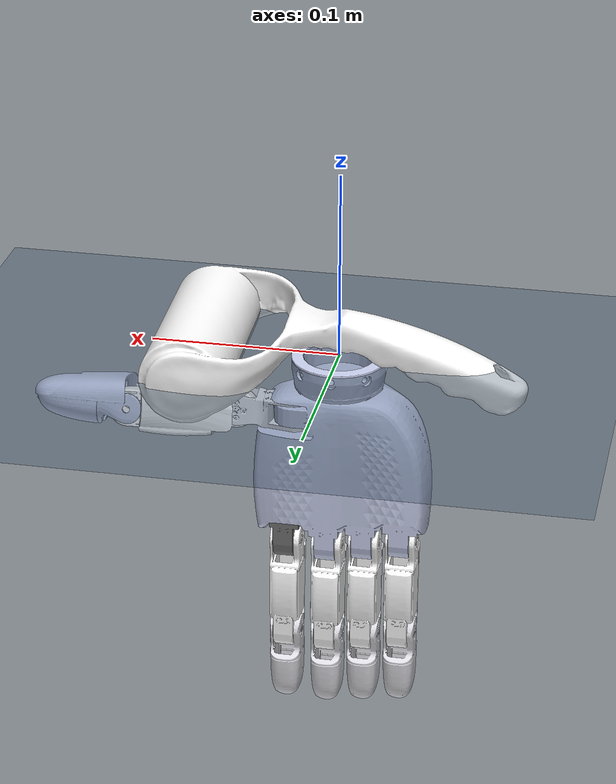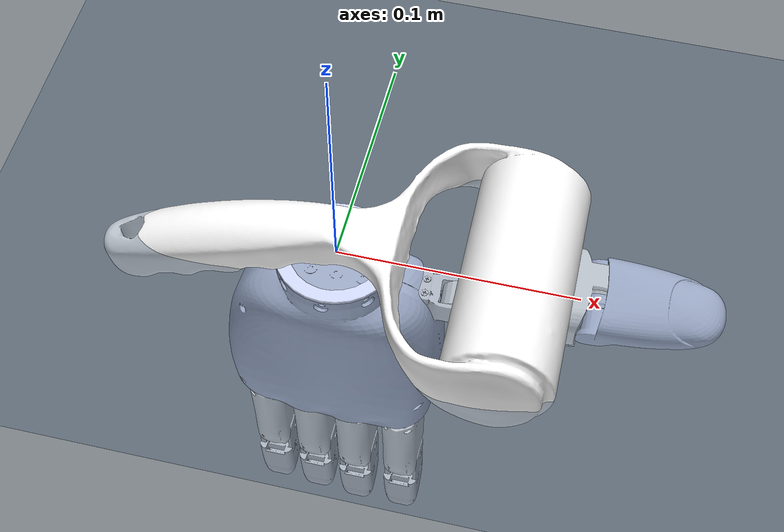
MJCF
<mujoco model="xhand_right">
  <compiler angle="radian" meshdir="../../../assets/" />
  <default>
    <joint armature="1" />
    <geom contype="0" conaffinity="0" condim="1" density="800" />
    <site group="3" rgba="1 0 0 1" />
    <general biastype="affine" gainprm="300" biasprm="0 -300 1" />
  </default>
  <asset>
    <texture type="skybox" colorspace="auto" builtin="gradient" rgb1="1 1 1" rgb2="1 1 1" width="512" height="3072" />
    <texture type="2d" colorspace="auto" name="right_groundplane" builtin="checker" mark="edge" rgb1="0.2 0.3 0.4" rgb2="0.1 0.2 0.3" markrgb="0.8 0.8 0.8" width="300" height="300" />
    <texture type="cube" colorspace="auto" name="skybox" builtin="gradient" rgb1="0.3 0.5 0.7" rgb2="0 0 0" width="512" height="3072" />
    <texture type="cube" colorspace="auto" name="groundplane" builtin="checker" mark="edge" rgb1="0.2 0.3 0.4" rgb2="0.1 0.2 0.3" markrgb="0.8 0.8 0.8" width="300" height="1800" />
    <material name="right_groundplane" texture="right_groundplane" texuniform="true" texrepeat="5 5" reflectance="0.2" />
    <material name="groundplane" texuniform="true" texrepeat="5 5" reflectance="0.2" />
    <mesh name="right_hand_link" content_type="model/stl" file="robots/xhand/assets/right_hand_link.STL" />
    <mesh name="right_hand_thumb_bend_link" content_type="model/stl" file="robots/xhand/assets/right_hand_thumb_bend_link.STL" />
    <mesh name="right_hand_thumb_rota_link1" content_type="model/stl" file="robots/xhand/assets/right_hand_thumb_rota_link1.STL" />
    <mesh name="right_hand_thumb_rota_link2" content_type="model/stl" file="robots/xhand/assets/right_hand_thumb_rota_link2.STL" />
    <mesh name="right_hand_index_bend_link" content_type="model/stl" file="robots/xhand/assets/right_hand_index_bend_link.STL" />
    <mesh name="right_hand_index_rota_link1" content_type="model/stl" file="robots/xhand/assets/right_hand_index_rota_link1.STL" />
    <mesh name="right_hand_index_rota_link2" content_type="model/stl" file="robots/xhand/assets/right_hand_index_rota_link2.STL" />
    <mesh name="right_hand_mid_link1" content_type="model/stl" file="robots/xhand/assets/right_hand_mid_link1.STL" />
    <mesh name="right_hand_mid_link2" content_type="model/stl" file="robots/xhand/assets/right_hand_mid_link2.STL" />
    <mesh name="right_hand_ring_link1" content_type="model/stl" file="robots/xhand/assets/right_hand_ring_link1.STL" />
    <mesh name="right_hand_ring_link2" content_type="model/stl" file="robots/xhand/assets/right_hand_ring_link2.STL" />
    <mesh name="right_hand_pinky_link1" content_type="model/stl" file="robots/xhand/assets/right_hand_pinky_link1.STL" />
    <mesh name="right_hand_pinky_link2" content_type="model/stl" file="robots/xhand/assets/right_hand_pinky_link2.STL" />
    <mesh name="right_visual" file="objects/031/visual.obj" />
    <mesh name="right_0" file="objects/031/convex/0.obj" />
    <mesh name="right_1" file="objects/031/convex/1.obj" />
    <mesh name="right_10" file="objects/031/convex/10.obj" />
    <mesh name="right_11" file="objects/031/convex/11.obj" />
    <mesh name="right_12" file="objects/031/convex/12.obj" />
    <mesh name="right_13" file="objects/031/convex/13.obj" />
    <mesh name="right_14" file="objects/031/convex/14.obj" />
    <mesh name="right_15" file="objects/031/convex/15.obj" />
    <mesh name="right_16" file="objects/031/convex/16.obj" />
    <mesh name="right_2" file="objects/031/convex/2.obj" />
    <mesh name="right_3" file="objects/031/convex/3.obj" />
    <mesh name="right_4" file="objects/031/convex/4.obj" />
    <mesh name="right_5" file="objects/031/convex/5.obj" />
    <mesh name="right_6" file="objects/031/convex/6.obj" />
    <mesh name="right_7" file="objects/031/convex/7.obj" />
    <mesh name="right_8" file="objects/031/convex/8.obj" />
    <mesh name="right_9" file="objects/031/convex/9.obj" />
  </asset>
  <worldbody>
    <geom name="floor" size="0 0 0.05" pos="0 0 -0.001" type="plane" material="right_groundplane" />
    <camera name="front" pos="0.031 0.941 0.844" quat="0.0150738 0.00673439 0.407848 0.912901" mode="trackcom" />
    <body name="R_forearm_ty_link">
      <inertial pos="0 0 0" mass="0.1" diaginertia="0.01 0.01 0.01" />
      <joint name="R_forearm_tx_link_joint" pos="0 0 0" axis="1 0 0" type="slide" range="-5 5" />
      <camera name="right_track" pos="-0.868 -0.348 -0.175" quat="0.493349 0.487956 0.506363 0.51196" />
      <body name="R_forearm_tz_link">
        <inertial pos="0 0 0" mass="0.1" diaginertia="0.01 0.01 0.01" />
        <joint name="R_forearm_ty_link_joint" pos="0 0 0" axis="0 1 0" type="slide" range="-5 5" />
        <body name="R_forearm_roll_link">
          <inertial pos="0 0 0" mass="0.1" diaginertia="0.01 0.01 0.01" />
          <joint name="R_forearm_tz_link_joint" pos="0 0 0" axis="0 0 1" type="slide" range="-5 5" />
          <body name="R_forearm_pitch_link">
            <inertial pos="0 0 0" mass="0.1" diaginertia="0.01 0.01 0.01" />
            <joint name="R_forearm_roll_link_joint" pos="0 0 0" axis="0 0 1" range="-6.2 6.2" />
            <body name="R_forearm_yaw_link">
              <inertial pos="0 0 0" mass="0.1" diaginertia="0.01 0.01 0.01" />
              <joint name="R_forearm_pitch_link_joint" pos="0 0 0" axis="1 0 0" range="-6.2 6.2" />
              <body name="right_hand_link">
                <inertial pos="-0.0071397 0.00342244 -0.0584807" quat="0.688453 0.098553 0.0886255 0.713068" mass="0.530025" diaginertia="0.00067782 0.000491189 0.000335821" />
                <joint name="R_forearm_yaw_link_joint" pos="0 0 0" axis="0 -1 0" range="-6.2 6.2" />
                <geom name="right_hand_link_visual" type="mesh" group="1" density="0" rgba="0.792157 0.819608 0.933333 1" mesh="right_hand_link" />
                <geom name="collision_hand_right_palm_0" size="0.04 0.024 0.04" pos="0 0 -0.06" type="box" group="3" rgba="0 1 0 1" />
                <site name="right_palm" pos="0 0 0" quat="0 0.707107 0.707107 0" size="0.01 0.02 0.03" type="box" />
                <body name="right_hand_thumb_bend_link" pos="0.0228 0.0095 -0.0305">
                  <inertial pos="0.0145291 -0.000901303 -0.000127926" quat="0.0288921 0.68936 0.0166971 0.72365" mass="0.00985529" diaginertia="1.30647e-06 1.29142e-06 5.40953e-07" />
                  <joint name="right_hand_thumb_bend_joint" pos="0 0 0" axis="0 0 1" range="0 1.83" />
                  <geom name="right_thumb_bend_visual" type="mesh" group="1" density="0" rgba="0.890196 0.890196 0.913725 1" mesh="right_hand_thumb_bend_link" />
                  <geom name="collision_hand_right_thumb_2" size="0.015 0.01" pos="0.01 0 0" quat="0.707107 0 -0.707107 0" type="capsule" group="3" rgba="0 1 0 1" />
                  <body name="right_hand_thumb_rota_link1" pos="0.028599 0.0083177 0.00178" quat="0.99124 0.130499 0.00265603 0.0201745">
                    <inertial pos="0.0279237 -0.000127603 -0.000272577" quat="-0.0989965 0.703671 0.0850598 0.698435" mass="0.153265" diaginertia="5.62327e-05 4.89801e-05 2.23924e-05" />
                    <joint name="right_hand_thumb_rota_joint1" pos="0 0 0" axis="0 1 0" range="-1.05 1.57" />
                    <geom name="right_thumb_rota1_visual" type="mesh" group="1" density="0" rgba="1 1 1 1" mesh="right_hand_thumb_rota_link1" />
                    <geom name="collision_hand_right_thumb_1" size="0.02 0.0275" pos="0.0275 0 0" quat="0.707107 0 -0.707107 0" type="capsule" group="3" rgba="0 1 0 1" />
                    <body name="right_hand_thumb_rota_link2" pos="0.0553 0 0">
                      <inertial pos="0.0224697 -0.000691342 0.00302232" quat="-0.0604029 0.715612 0.0198067 0.695599" mass="0.0374004" diaginertia="9.5465e-06 8.27017e-06 3.92137e-06" />
                      <joint name="right_hand_thumb_rota_joint2" pos="0 0 0" axis="0 1 0" range="-0.175 1.83" />
                      <geom name="right_thumb_rota2_visual" type="mesh" group="1" density="0" rgba="0.792157 0.819608 0.933333 1" mesh="right_hand_thumb_rota_link2" />
                      <geom name="collision_hand_right_thumb_0" size="0.015 0.02" pos="0.02 0 0" quat="0.707107 0 -0.707107 0" type="capsule" group="3" rgba="0 1 0 1" />
                      <geom size="0.001" pos="0.0504025 0 0" group="1" density="0" rgba="0.698039 0.698039 0.698039 1" />
                      <site name="right_thumb_tip" pos="0.04 0 -0.012" />
                      <site name="track_hand_right_thumb_tip" pos="0.04 0 -0.012" />
                      <site name="trace_hand_right_thumb_tip" pos="0.04 0 -0.012" />
                    </body>
                  </body>
                </body>
                <body name="right_hand_index_bend_link" pos="0.0265 0.0065 -0.0899">
                  <inertial pos="8.08449e-05 0.000675884 0.00420851" quat="0.999802 -0.0189928 -0.00582288 0.000998418" mass="0.0677836" diaginertia="2.16592e-05 2.09943e-05 3.36803e-06" />
                  <joint name="right_hand_index_bend_joint" pos="0 0 0" axis="0 1 0" range="-0.175 0.175" />
                  <geom name="right_index_bend_visual" type="mesh" group="1" density="0" rgba="0.439216 0.439216 0.439216 1" mesh="right_hand_index_bend_link" />
                  <body name="right_hand_index_rota_link1" pos="0 0 -0.0178">
                    <inertial pos="-0.00013977 -0.000800517 -0.0356039" quat="0.999865 0.00809183 -0.0131314 0.00566198" mass="0.0630216" diaginertia="2.05301e-05 1.92461e-05 4.135e-06" />
                    <joint name="right_hand_index_joint1" pos="0 0 0" axis="1 0 0" range="0 1.92" />
                    <geom name="right_index_rota1_visual" type="mesh" group="1" density="0" rgba="1 1 1 1" mesh="right_hand_index_rota_link1" />
                    <geom name="collision_hand_right_index_1" size="0.012 0.0275" pos="0 0 -0.0275" type="capsule" group="3" rgba="0 1 0 1" />
                    <body name="right_hand_index_rota_link2" pos="0 0 -0.0558">
                      <inertial pos="-0.000338569 1.93676e-05 -0.0231329" quat="0.935384 0.00588977 -0.0260883 0.35262" mass="0.0179923" diaginertia="3.02409e-06 3.01968e-06 9.82703e-07" />
                      <joint name="right_hand_index_joint2" pos="0 0 0" axis="1 0 0" range="0 1.92" />
                      <geom name="right_index_rota2_visual" type="mesh" group="1" density="0" rgba="0.866667 0.866667 0.890196 1" mesh="right_hand_index_rota_link2" />
                      <geom name="collision_hand_right_index_0" size="0.01 0.015" pos="0 0 -0.015" type="capsule" group="3" rgba="0 1 0 1" />
                      <geom size="0.001" pos="0 0 -0.0425" group="1" density="0" rgba="0.698039 0.698039 0.698039 1" />
                      <site name="right_index_tip" pos="0 0.004 -0.027" />
                      <site name="track_hand_right_index_tip" pos="0 0.004 -0.027" />
                      <site name="trace_hand_right_index_tip" pos="0 0.004 -0.027" />
                    </body>
                  </body>
                </body>
                <body name="right_hand_mid_link1" pos="0.004 0.0065 -0.1082">
                  <inertial pos="-0.000139769 -0.000800517 -0.0356039" quat="0.999865 0.00809181 -0.0131314 0.00566199" mass="0.0630216" diaginertia="2.05301e-05 1.92461e-05 4.135e-06" />
                  <joint name="right_hand_mid_joint1" pos="0 0 0" axis="1 0 0" range="0 1.92" />
                  <geom name="right_middle_link1_visual" type="mesh" group="1" density="0" rgba="1 1 1 1" mesh="right_hand_mid_link1" />
                  <geom name="collision_hand_right_middle_1" size="0.012 0.0275" pos="0 0 -0.0275" type="capsule" group="3" rgba="0 1 0 1" />
                  <body name="right_hand_mid_link2" pos="0 0 -0.0558">
                    <inertial pos="-0.000338569 1.93676e-05 -0.0231329" quat="0.935384 0.00588977 -0.0260883 0.35262" mass="0.0179923" diaginertia="3.02409e-06 3.01968e-06 9.82703e-07" />
                    <joint name="right_hand_mid_joint2" pos="0 0 0" axis="1 0 0" range="0 1.94" />
                    <geom name="right_middle_link2_visual" type="mesh" group="1" density="0" rgba="0.866667 0.866667 0.890196 1" mesh="right_hand_mid_link2" />
                    <geom name="collision_hand_right_middle_0" size="0.01 0.015" pos="0 0 -0.015" type="capsule" group="3" rgba="0 1 0 1" />
                    <geom size="0.001" pos="0 0 -0.042107" group="1" density="0" rgba="0.698039 0.698039 0.698039 1" />
                    <site name="right_middle_tip" pos="0 0.004 -0.027" />
                    <site name="track_hand_right_middle_tip" pos="0 0.004 -0.027" />
                    <site name="trace_hand_right_middle_tip" pos="0 0.004 -0.027" />
                  </body>
                </body>
                <body name="right_hand_ring_link1" pos="-0.016 0.0065 -0.1052">
                  <inertial pos="-0.00013977 -0.000800517 -0.0356039" quat="0.999865 0.00809183 -0.0131314 0.00566196" mass="0.0630216" diaginertia="2.05301e-05 1.92461e-05 4.135e-06" />
                  <joint name="right_hand_ring_joint1" pos="0 0 0" axis="1 0 0" range="0 1.92" />
                  <geom name="right_ring_link1_visual" type="mesh" group="1" density="0" rgba="1 1 1 1" mesh="right_hand_ring_link1" />
                  <geom name="collision_hand_right_ring_1" size="0.012 0.0275" pos="0 0 -0.0275" type="capsule" group="3" rgba="0 1 0 1" />
                  <body name="right_hand_ring_link2" pos="0 0 -0.0558">
                    <inertial pos="-0.000338573 1.93622e-05 -0.0231328" quat="0.935372 0.00588872 -0.0260882 0.352652" mass="0.0179923" diaginertia="3.02409e-06 3.01968e-06 9.82702e-07" />
                    <joint name="right_hand_ring_joint2" pos="0 0 0" axis="1 0 0" range="0 1.92" />
                    <geom name="right_ring_link2_visual" type="mesh" group="1" density="0" rgba="0.866667 0.866667 0.890196 1" mesh="right_hand_ring_link2" />
                    <geom name="collision_hand_right_ring_0" size="0.01 0.015" pos="0 0 -0.015" type="capsule" group="3" rgba="0 1 0 1" />
                    <geom size="0.001" pos="0 0 -0.0425" group="1" density="0" rgba="0.698039 0.698039 0.698039 1" />
                    <site name="right_ring_tip" pos="0 0.004 -0.027" />
                    <site name="track_hand_right_ring_tip" pos="0 0.004 -0.027" />
                    <site name="trace_hand_right_ring_tip" pos="0 0.004 -0.027" />
                  </body>
                </body>
                <body name="right_hand_pinky_link1" pos="-0.036 0.0065 -0.1022">
                  <inertial pos="-0.000139769 -0.000800517 -0.0356039" quat="0.999865 0.00809181 -0.0131314 0.00566204" mass="0.0630216" diaginertia="2.05301e-05 1.92461e-05 4.135e-06" />
                  <joint name="right_hand_pinky_joint1" pos="0 0 0" axis="1 0 0" range="0 1.92" />
                  <geom name="right_pinky_link1_visual" type="mesh" group="1" density="0" rgba="1 1 1 1" mesh="right_hand_pinky_link1" />
                  <geom name="collision_hand_right_pinky_1" size="0.012 0.0275" pos="0 0 -0.0275" type="capsule" group="3" rgba="0 1 0 1" />
                  <body name="right_hand_pinky_link2" pos="0 0 -0.0558">
                    <inertial pos="-0.000338569 1.93676e-05 -0.0231329" quat="0.935384 0.00588976 -0.0260883 0.352621" mass="0.0179923" diaginertia="3.02409e-06 3.01968e-06 9.82703e-07" />
                    <joint name="right_hand_pinky_joint2" pos="0 0 0" axis="1 0 0" range="0 1.92" />
                    <geom name="right_pinky_link2_visual" type="mesh" group="1" density="0" rgba="0.866667 0.866667 0.890196 1" mesh="right_hand_pinky_link2" />
                    <geom name="collision_hand_right_pinky_0" size="0.01 0.015" pos="0 0 -0.015" type="capsule" group="3" rgba="0 1 0 1" />
                    <geom size="0.001" pos="0 0 -0.0425" group="1" density="0" rgba="0.698039 0.698039 0.698039 1" />
                    <site name="right_pinky_tip" pos="0 0.004 -0.027" />
                    <site name="track_hand_right_pinky_tip" pos="0 0.004 -0.027" />
                    <site name="trace_hand_right_pinky_tip" pos="0 0.004 -0.027" />
                  </body>
                </body>
              </body>
            </body>
          </body>
        </body>
      </body>
    </body>
    <body name="right_object">
      <joint name="right_object_pos_x" type="slide" axis="1 0 0" armature="0.0001" frictionloss="0.0001" />
      <joint name="right_object_pos_y" type="slide" axis="0 1 0" armature="0.0001" frictionloss="0.0001" />
      <joint name="right_object_pos_z" type="slide" axis="0 0 1" armature="0.0001" frictionloss="0.0001" />
      <joint name="right_object_rot_x" type="hinge" axis="1 0 0" armature="0.0001" frictionloss="0.0001" />
      <joint name="right_object_rot_y" type="hinge" axis="0 1 0" armature="0.0001" frictionloss="0.0001" />
      <joint name="right_object_rot_z" type="hinge" axis="0 0 1" armature="0.0001" frictionloss="0.0001" />
      <geom name="right_object_0" type="mesh" group="3" density="1000" rgba="0 1 0 1" mesh="right_0" />
      <geom name="right_object_1" type="mesh" group="3" density="1000" rgba="0 1 0 1" mesh="right_1" />
      <geom name="right_object_10" type="mesh" group="3" density="1000" rgba="0 1 0 1" mesh="right_10" />
      <geom name="right_object_11" type="mesh" group="3" density="1000" rgba="0 1 0 1" mesh="right_11" />
      <geom name="right_object_12" type="mesh" group="3" density="1000" rgba="0 1 0 1" mesh="right_12" />
      <geom name="right_object_13" type="mesh" group="3" density="1000" rgba="0 1 0 1" mesh="right_13" />
      <geom name="right_object_14" type="mesh" group="3" density="1000" rgba="0 1 0 1" mesh="right_14" />
      <geom name="right_object_15" type="mesh" group="3" density="1000" rgba="0 1 0 1" mesh="right_15" />
      <geom name="right_object_16" type="mesh" group="3" density="1000" rgba="0 1 0 1" mesh="right_16" />
      <geom name="right_object_2" type="mesh" group="3" density="1000" rgba="0 1 0 1" mesh="right_2" />
      <geom name="right_object_3" type="mesh" group="3" density="1000" rgba="0 1 0 1" mesh="right_3" />
      <geom name="right_object_4" type="mesh" group="3" density="1000" rgba="0 1 0 1" mesh="right_4" />
      <geom name="right_object_5" type="mesh" group="3" density="1000" rgba="0 1 0 1" mesh="right_5" />
      <geom name="right_object_6" type="mesh" group="3" density="1000" rgba="0 1 0 1" mesh="right_6" />
      <geom name="right_object_7" type="mesh" group="3" density="1000" rgba="0 1 0 1" mesh="right_7" />
      <geom name="right_object_8" type="mesh" group="3" density="1000" rgba="0 1 0 1" mesh="right_8" />
      <geom name="right_object_9" type="mesh" group="3" density="1000" rgba="0 1 0 1" mesh="right_9" />
      <geom name="right_object_visual" type="mesh" density="0" rgba="1 1 1 1" mesh="right_visual" />
      <site name="right_object" pos="0 0 0" size="0.01 0.02 0.03" type="box" />
      <site name="trace_right_object" pos="0 0 0" size="0.01" group="4" rgba="0 1 0 1" />
      <site name="track_object_right_thumb_tip" pos="0 0 0" size="0.01" group="4" rgba="0 1 0 1" />
      <site name="track_object_right_index_tip" pos="0 0 0" size="0.01" group="4" rgba="0 1 0 1" />
      <site name="track_object_right_middle_tip" pos="0 0 0" size="0.01" group="4" rgba="0 1 0 1" />
      <site name="track_object_right_ring_tip" pos="0 0 0" size="0.01" group="4" rgba="0 1 0 1" />
      <site name="track_object_right_pinky_tip" pos="0 0 0" size="0.01" group="4" rgba="0 1 0 1" />
    </body>
    <body name="ref_object_right_thumb_tip" mocap="true">
      <site name="ref_object_right_thumb_tip" pos="0 0 0" size="0.02" group="4" rgba="0 1 0 1" />
    </body>
    <body name="ref_hand_right_thumb_tip" mocap="true">
      <site name="ref_hand_right_thumb_tip" pos="0 0 0" size="0.02" group="4" rgba="0 1 0 1" />
    </body>
    <body name="ref_object_right_index_tip" mocap="true">
      <site name="ref_object_right_index_tip" pos="0 0 0" size="0.02" group="4" rgba="0 1 0 1" />
    </body>
    <body name="ref_hand_right_index_tip" mocap="true">
      <site name="ref_hand_right_index_tip" pos="0 0 0" size="0.02" group="4" rgba="0 1 0 1" />
    </body>
    <body name="ref_object_right_middle_tip" mocap="true">
      <site name="ref_object_right_middle_tip" pos="0 0 0" size="0.02" group="4" rgba="0 1 0 1" />
    </body>
    <body name="ref_hand_right_middle_tip" mocap="true">
      <site name="ref_hand_right_middle_tip" pos="0 0 0" size="0.02" group="4" rgba="0 1 0 1" />
    </body>
    <body name="ref_object_right_ring_tip" mocap="true">
      <site name="ref_object_right_ring_tip" pos="0 0 0" size="0.02" group="4" rgba="0 1 0 1" />
    </body>
    <body name="ref_hand_right_ring_tip" mocap="true">
      <site name="ref_hand_right_ring_tip" pos="0 0 0" size="0.02" group="4" rgba="0 1 0 1" />
    </body>
    <body name="ref_object_right_pinky_tip" mocap="true">
      <site name="ref_object_right_pinky_tip" pos="0 0 0" size="0.02" group="4" rgba="0 1 0 1" />
    </body>
    <body name="ref_hand_right_pinky_tip" mocap="true">
      <site name="ref_hand_right_pinky_tip" pos="0 0 0" size="0.02" group="4" rgba="0 1 0 1" />
    </body>
  </worldbody>
  <contact>
    <pair geom1="floor" geom2="right_object_0" name="floor_right_object_0" friction="1 1 0.1 0 0" />
    <pair geom1="floor" geom2="right_object_1" name="floor_right_object_1" friction="1 1 0.1 0 0" />
    <pair geom1="floor" geom2="right_object_10" name="floor_right_object_10" friction="1 1 0.1 0 0" />
    <pair geom1="floor" geom2="right_object_11" name="floor_right_object_11" friction="1 1 0.1 0 0" />
    <pair geom1="floor" geom2="right_object_12" name="floor_right_object_12" friction="1 1 0.1 0 0" />
    <pair geom1="floor" geom2="right_object_13" name="floor_right_object_13" friction="1 1 0.1 0 0" />
    <pair geom1="floor" geom2="right_object_14" name="floor_right_object_14" friction="1 1 0.1 0 0" />
    <pair geom1="floor" geom2="right_object_15" name="floor_right_object_15" friction="1 1 0.1 0 0" />
    <pair geom1="floor" geom2="right_object_16" name="floor_right_object_16" friction="1 1 0.1 0 0" />
    <pair geom1="floor" geom2="right_object_2" name="floor_right_object_2" friction="1 1 0.1 0 0" />
    <pair geom1="floor" geom2="right_object_3" name="floor_right_object_3" friction="1 1 0.1 0 0" />
    <pair geom1="floor" geom2="right_object_4" name="floor_right_object_4" friction="1 1 0.1 0 0" />
    <pair geom1="floor" geom2="right_object_5" name="floor_right_object_5" friction="1 1 0.1 0 0" />
    <pair geom1="floor" geom2="right_object_6" name="floor_right_object_6" friction="1 1 0.1 0 0" />
    <pair geom1="floor" geom2="right_object_7" name="floor_right_object_7" friction="1 1 0.1 0 0" />
    <pair geom1="floor" geom2="right_object_8" name="floor_right_object_8" friction="1 1 0.1 0 0" />
    <pair geom1="floor" geom2="right_object_9" name="floor_right_object_9" friction="1 1 0.1 0 0" />
    <pair geom1="collision_hand_right_palm_0" geom2="collision_hand_right_thumb_0" name="collision_hand_right_palm_0_collision_hand_right_thumb_0" friction="1 1 0.1 0 0" />
    <pair geom1="collision_hand_right_palm_0" geom2="collision_hand_right_index_0" name="collision_hand_right_palm_0_collision_hand_right_index_0" friction="1 1 0.1 0 0" />
    <pair geom1="collision_hand_right_palm_0" geom2="collision_hand_right_middle_0" name="collision_hand_right_palm_0_collision_hand_right_middle_0" friction="1 1 0.1 0 0" />
    <pair geom1="collision_hand_right_palm_0" geom2="collision_hand_right_ring_0" name="collision_hand_right_palm_0_collision_hand_right_ring_0" friction="1 1 0.1 0 0" />
    <pair geom1="collision_hand_right_palm_0" geom2="collision_hand_right_pinky_0" name="collision_hand_right_palm_0_collision_hand_right_pinky_0" friction="1 1 0.1 0 0" />
    <pair geom1="collision_hand_right_palm_0" geom2="right_object_0" name="collision_hand_right_palm_0_right_object_0" friction="1 1 0.1 0 0" />
    <pair geom1="collision_hand_right_palm_0" geom2="right_object_1" name="collision_hand_right_palm_0_right_object_1" friction="1 1 0.1 0 0" />
    <pair geom1="collision_hand_right_palm_0" geom2="right_object_10" name="collision_hand_right_palm_0_right_object_10" friction="1 1 0.1 0 0" />
    <pair geom1="collision_hand_right_palm_0" geom2="right_object_11" name="collision_hand_right_palm_0_right_object_11" friction="1 1 0.1 0 0" />
    <pair geom1="collision_hand_right_palm_0" geom2="right_object_12" name="collision_hand_right_palm_0_right_object_12" friction="1 1 0.1 0 0" />
    <pair geom1="collision_hand_right_palm_0" geom2="right_object_13" name="collision_hand_right_palm_0_right_object_13" friction="1 1 0.1 0 0" />
    <pair geom1="collision_hand_right_palm_0" geom2="right_object_14" name="collision_hand_right_palm_0_right_object_14" friction="1 1 0.1 0 0" />
    <pair geom1="collision_hand_right_palm_0" geom2="right_object_15" name="collision_hand_right_palm_0_right_object_15" friction="1 1 0.1 0 0" />
    <pair geom1="collision_hand_right_palm_0" geom2="right_object_16" name="collision_hand_right_palm_0_right_object_16" friction="1 1 0.1 0 0" />
    <pair geom1="collision_hand_right_palm_0" geom2="right_object_2" name="collision_hand_right_palm_0_right_object_2" friction="1 1 0.1 0 0" />
    <pair geom1="collision_hand_right_palm_0" geom2="right_object_3" name="collision_hand_right_palm_0_right_object_3" friction="1 1 0.1 0 0" />
    <pair geom1="collision_hand_right_palm_0" geom2="right_object_4" name="collision_hand_right_palm_0_right_object_4" friction="1 1 0.1 0 0" />
    <pair geom1="collision_hand_right_palm_0" geom2="right_object_5" name="collision_hand_right_palm_0_right_object_5" friction="1 1 0.1 0 0" />
    <pair geom1="collision_hand_right_palm_0" geom2="right_object_6" name="collision_hand_right_palm_0_right_object_6" friction="1 1 0.1 0 0" />
    <pair geom1="collision_hand_right_palm_0" geom2="right_object_7" name="collision_hand_right_palm_0_right_object_7" friction="1 1 0.1 0 0" />
    <pair geom1="collision_hand_right_palm_0" geom2="right_object_8" name="collision_hand_right_palm_0_right_object_8" friction="1 1 0.1 0 0" />
    <pair geom1="collision_hand_right_palm_0" geom2="right_object_9" name="collision_hand_right_palm_0_right_object_9" friction="1 1 0.1 0 0" />
    <pair geom1="collision_hand_right_thumb_2" geom2="right_object_0" name="collision_hand_right_thumb_2_right_object_0" condim="4" friction="1 1 0.1 0 0" />
    <pair geom1="collision_hand_right_thumb_2" geom2="right_object_1" name="collision_hand_right_thumb_2_right_object_1" condim="4" friction="1 1 0.1 0 0" />
    <pair geom1="collision_hand_right_thumb_2" geom2="right_object_10" name="collision_hand_right_thumb_2_right_object_10" condim="4" friction="1 1 0.1 0 0" />
    <pair geom1="collision_hand_right_thumb_2" geom2="right_object_11" name="collision_hand_right_thumb_2_right_object_11" condim="4" friction="1 1 0.1 0 0" />
    <pair geom1="collision_hand_right_thumb_2" geom2="right_object_12" name="collision_hand_right_thumb_2_right_object_12" condim="4" friction="1 1 0.1 0 0" />
    <pair geom1="collision_hand_right_thumb_2" geom2="right_object_13" name="collision_hand_right_thumb_2_right_object_13" condim="4" friction="1 1 0.1 0 0" />
    <pair geom1="collision_hand_right_thumb_2" geom2="right_object_14" name="collision_hand_right_thumb_2_right_object_14" condim="4" friction="1 1 0.1 0 0" />
    <pair geom1="collision_hand_right_thumb_2" geom2="right_object_15" name="collision_hand_right_thumb_2_right_object_15" condim="4" friction="1 1 0.1 0 0" />
    <pair geom1="collision_hand_right_thumb_2" geom2="right_object_16" name="collision_hand_right_thumb_2_right_object_16" condim="4" friction="1 1 0.1 0 0" />
    <pair geom1="collision_hand_right_thumb_2" geom2="right_object_2" name="collision_hand_right_thumb_2_right_object_2" condim="4" friction="1 1 0.1 0 0" />
    <pair geom1="collision_hand_right_thumb_2" geom2="right_object_3" name="collision_hand_right_thumb_2_right_object_3" condim="4" friction="1 1 0.1 0 0" />
    <pair geom1="collision_hand_right_thumb_2" geom2="right_object_4" name="collision_hand_right_thumb_2_right_object_4" condim="4" friction="1 1 0.1 0 0" />
    <pair geom1="collision_hand_right_thumb_2" geom2="right_object_5" name="collision_hand_right_thumb_2_right_object_5" condim="4" friction="1 1 0.1 0 0" />
    <pair geom1="collision_hand_right_thumb_2" geom2="right_object_6" name="collision_hand_right_thumb_2_right_object_6" condim="4" friction="1 1 0.1 0 0" />
    <pair geom1="collision_hand_right_thumb_2" geom2="right_object_7" name="collision_hand_right_thumb_2_right_object_7" condim="4" friction="1 1 0.1 0 0" />
    <pair geom1="collision_hand_right_thumb_2" geom2="right_object_8" name="collision_hand_right_thumb_2_right_object_8" condim="4" friction="1 1 0.1 0 0" />
    <pair geom1="collision_hand_right_thumb_2" geom2="right_object_9" name="collision_hand_right_thumb_2_right_object_9" condim="4" friction="1 1 0.1 0 0" />
    <pair geom1="collision_hand_right_thumb_1" geom2="right_object_0" name="collision_hand_right_thumb_1_right_object_0" condim="4" friction="1 1 0.1 0 0" />
    <pair geom1="collision_hand_right_thumb_1" geom2="right_object_1" name="collision_hand_right_thumb_1_right_object_1" condim="4" friction="1 1 0.1 0 0" />
    <pair geom1="collision_hand_right_thumb_1" geom2="right_object_10" name="collision_hand_right_thumb_1_right_object_10" condim="4" friction="1 1 0.1 0 0" />
    <pair geom1="collision_hand_right_thumb_1" geom2="right_object_11" name="collision_hand_right_thumb_1_right_object_11" condim="4" friction="1 1 0.1 0 0" />
    <pair geom1="collision_hand_right_thumb_1" geom2="right_object_12" name="collision_hand_right_thumb_1_right_object_12" condim="4" friction="1 1 0.1 0 0" />
    <pair geom1="collision_hand_right_thumb_1" geom2="right_object_13" name="collision_hand_right_thumb_1_right_object_13" condim="4" friction="1 1 0.1 0 0" />
    <pair geom1="collision_hand_right_thumb_1" geom2="right_object_14" name="collision_hand_right_thumb_1_right_object_14" condim="4" friction="1 1 0.1 0 0" />
    <pair geom1="collision_hand_right_thumb_1" geom2="right_object_15" name="collision_hand_right_thumb_1_right_object_15" condim="4" friction="1 1 0.1 0 0" />
    <pair geom1="collision_hand_right_thumb_1" geom2="right_object_16" name="collision_hand_right_thumb_1_right_object_16" condim="4" friction="1 1 0.1 0 0" />
    <pair geom1="collision_hand_right_thumb_1" geom2="right_object_2" name="collision_hand_right_thumb_1_right_object_2" condim="4" friction="1 1 0.1 0 0" />
    <pair geom1="collision_hand_right_thumb_1" geom2="right_object_3" name="collision_hand_right_thumb_1_right_object_3" condim="4" friction="1 1 0.1 0 0" />
    <pair geom1="collision_hand_right_thumb_1" geom2="right_object_4" name="collision_hand_right_thumb_1_right_object_4" condim="4" friction="1 1 0.1 0 0" />
    <pair geom1="collision_hand_right_thumb_1" geom2="right_object_5" name="collision_hand_right_thumb_1_right_object_5" condim="4" friction="1 1 0.1 0 0" />
    <pair geom1="collision_hand_right_thumb_1" geom2="right_object_6" name="collision_hand_right_thumb_1_right_object_6" condim="4" friction="1 1 0.1 0 0" />
    <pair geom1="collision_hand_right_thumb_1" geom2="right_object_7" name="collision_hand_right_thumb_1_right_object_7" condim="4" friction="1 1 0.1 0 0" />
    <pair geom1="collision_hand_right_thumb_1" geom2="right_object_8" name="collision_hand_right_thumb_1_right_object_8" condim="4" friction="1 1 0.1 0 0" />
    <pair geom1="collision_hand_right_thumb_1" geom2="right_object_9" name="collision_hand_right_thumb_1_right_object_9" condim="4" friction="1 1 0.1 0 0" />
    <pair geom1="collision_hand_right_thumb_0" geom2="collision_hand_right_index_0" name="collision_hand_right_thumb_0_collision_hand_right_index_0" friction="1 1 0.1 0 0" />
    <pair geom1="collision_hand_right_thumb_0" geom2="collision_hand_right_middle_0" name="collision_hand_right_thumb_0_collision_hand_right_middle_0" friction="1 1 0.1 0 0" />
    <pair geom1="collision_hand_right_thumb_0" geom2="collision_hand_right_ring_0" name="collision_hand_right_thumb_0_collision_hand_right_ring_0" friction="1 1 0.1 0 0" />
    <pair geom1="collision_hand_right_thumb_0" geom2="collision_hand_right_pinky_0" name="collision_hand_right_thumb_0_collision_hand_right_pinky_0" friction="1 1 0.1 0 0" />
    <pair geom1="collision_hand_right_thumb_0" geom2="right_object_0" name="collision_hand_right_thumb_0_right_object_0" condim="4" friction="1 1 0.1 0 0" />
    <pair geom1="collision_hand_right_thumb_0" geom2="right_object_1" name="collision_hand_right_thumb_0_right_object_1" condim="4" friction="1 1 0.1 0 0" />
    <pair geom1="collision_hand_right_thumb_0" geom2="right_object_10" name="collision_hand_right_thumb_0_right_object_10" condim="4" friction="1 1 0.1 0 0" />
    <pair geom1="collision_hand_right_thumb_0" geom2="right_object_11" name="collision_hand_right_thumb_0_right_object_11" condim="4" friction="1 1 0.1 0 0" />
    <pair geom1="collision_hand_right_thumb_0" geom2="right_object_12" name="collision_hand_right_thumb_0_right_object_12" condim="4" friction="1 1 0.1 0 0" />
    <pair geom1="collision_hand_right_thumb_0" geom2="right_object_13" name="collision_hand_right_thumb_0_right_object_13" condim="4" friction="1 1 0.1 0 0" />
    <pair geom1="collision_hand_right_thumb_0" geom2="right_object_14" name="collision_hand_right_thumb_0_right_object_14" condim="4" friction="1 1 0.1 0 0" />
    <pair geom1="collision_hand_right_thumb_0" geom2="right_object_15" name="collision_hand_right_thumb_0_right_object_15" condim="4" friction="1 1 0.1 0 0" />
    <pair geom1="collision_hand_right_thumb_0" geom2="right_object_16" name="collision_hand_right_thumb_0_right_object_16" condim="4" friction="1 1 0.1 0 0" />
    <pair geom1="collision_hand_right_thumb_0" geom2="right_object_2" name="collision_hand_right_thumb_0_right_object_2" condim="4" friction="1 1 0.1 0 0" />
    <pair geom1="collision_hand_right_thumb_0" geom2="right_object_3" name="collision_hand_right_thumb_0_right_object_3" condim="4" friction="1 1 0.1 0 0" />
    <pair geom1="collision_hand_right_thumb_0" geom2="right_object_4" name="collision_hand_right_thumb_0_right_object_4" condim="4" friction="1 1 0.1 0 0" />
    <pair geom1="collision_hand_right_thumb_0" geom2="right_object_5" name="collision_hand_right_thumb_0_right_object_5" condim="4" friction="1 1 0.1 0 0" />
    <pair geom1="collision_hand_right_thumb_0" geom2="right_object_6" name="collision_hand_right_thumb_0_right_object_6" condim="4" friction="1 1 0.1 0 0" />
    <pair geom1="collision_hand_right_thumb_0" geom2="right_object_7" name="collision_hand_right_thumb_0_right_object_7" condim="4" friction="1 1 0.1 0 0" />
    <pair geom1="collision_hand_right_thumb_0" geom2="right_object_8" name="collision_hand_right_thumb_0_right_object_8" condim="4" friction="1 1 0.1 0 0" />
    <pair geom1="collision_hand_right_thumb_0" geom2="right_object_9" name="collision_hand_right_thumb_0_right_object_9" condim="4" friction="1 1 0.1 0 0" />
    <pair geom1="collision_hand_right_index_1" geom2="right_object_0" name="collision_hand_right_index_1_right_object_0" condim="4" friction="1 1 0.1 0 0" />
    <pair geom1="collision_hand_right_index_1" geom2="right_object_1" name="collision_hand_right_index_1_right_object_1" condim="4" friction="1 1 0.1 0 0" />
    <pair geom1="collision_hand_right_index_1" geom2="right_object_10" name="collision_hand_right_index_1_right_object_10" condim="4" friction="1 1 0.1 0 0" />
    <pair geom1="collision_hand_right_index_1" geom2="right_object_11" name="collision_hand_right_index_1_right_object_11" condim="4" friction="1 1 0.1 0 0" />
    <pair geom1="collision_hand_right_index_1" geom2="right_object_12" name="collision_hand_right_index_1_right_object_12" condim="4" friction="1 1 0.1 0 0" />
    <pair geom1="collision_hand_right_index_1" geom2="right_object_13" name="collision_hand_right_index_1_right_object_13" condim="4" friction="1 1 0.1 0 0" />
    <pair geom1="collision_hand_right_index_1" geom2="right_object_14" name="collision_hand_right_index_1_right_object_14" condim="4" friction="1 1 0.1 0 0" />
    <pair geom1="collision_hand_right_index_1" geom2="right_object_15" name="collision_hand_right_index_1_right_object_15" condim="4" friction="1 1 0.1 0 0" />
    <pair geom1="collision_hand_right_index_1" geom2="right_object_16" name="collision_hand_right_index_1_right_object_16" condim="4" friction="1 1 0.1 0 0" />
    <pair geom1="collision_hand_right_index_1" geom2="right_object_2" name="collision_hand_right_index_1_right_object_2" condim="4" friction="1 1 0.1 0 0" />
    <pair geom1="collision_hand_right_index_1" geom2="right_object_3" name="collision_hand_right_index_1_right_object_3" condim="4" friction="1 1 0.1 0 0" />
    <pair geom1="collision_hand_right_index_1" geom2="right_object_4" name="collision_hand_right_index_1_right_object_4" condim="4" friction="1 1 0.1 0 0" />
    <pair geom1="collision_hand_right_index_1" geom2="right_object_5" name="collision_hand_right_index_1_right_object_5" condim="4" friction="1 1 0.1 0 0" />
    <pair geom1="collision_hand_right_index_1" geom2="right_object_6" name="collision_hand_right_index_1_right_object_6" condim="4" friction="1 1 0.1 0 0" />
    <pair geom1="collision_hand_right_index_1" geom2="right_object_7" name="collision_hand_right_index_1_right_object_7" condim="4" friction="1 1 0.1 0 0" />
    <pair geom1="collision_hand_right_index_1" geom2="right_object_8" name="collision_hand_right_index_1_right_object_8" condim="4" friction="1 1 0.1 0 0" />
    <pair geom1="collision_hand_right_index_1" geom2="right_object_9" name="collision_hand_right_index_1_right_object_9" condim="4" friction="1 1 0.1 0 0" />
    <pair geom1="collision_hand_right_index_0" geom2="collision_hand_right_middle_0" name="collision_hand_right_index_0_collision_hand_right_middle_0" friction="1 1 0.1 0 0" />
    <pair geom1="collision_hand_right_index_0" geom2="collision_hand_right_ring_0" name="collision_hand_right_index_0_collision_hand_right_ring_0" friction="1 1 0.1 0 0" />
    <pair geom1="collision_hand_right_index_0" geom2="collision_hand_right_pinky_0" name="collision_hand_right_index_0_collision_hand_right_pinky_0" friction="1 1 0.1 0 0" />
    <pair geom1="collision_hand_right_index_0" geom2="right_object_0" name="collision_hand_right_index_0_right_object_0" condim="4" friction="1 1 0.1 0 0" />
    <pair geom1="collision_hand_right_index_0" geom2="right_object_1" name="collision_hand_right_index_0_right_object_1" condim="4" friction="1 1 0.1 0 0" />
    <pair geom1="collision_hand_right_index_0" geom2="right_object_10" name="collision_hand_right_index_0_right_object_10" condim="4" friction="1 1 0.1 0 0" />
    <pair geom1="collision_hand_right_index_0" geom2="right_object_11" name="collision_hand_right_index_0_right_object_11" condim="4" friction="1 1 0.1 0 0" />
    <pair geom1="collision_hand_right_index_0" geom2="right_object_12" name="collision_hand_right_index_0_right_object_12" condim="4" friction="1 1 0.1 0 0" />
    <pair geom1="collision_hand_right_index_0" geom2="right_object_13" name="collision_hand_right_index_0_right_object_13" condim="4" friction="1 1 0.1 0 0" />
    <pair geom1="collision_hand_right_index_0" geom2="right_object_14" name="collision_hand_right_index_0_right_object_14" condim="4" friction="1 1 0.1 0 0" />
    <pair geom1="collision_hand_right_index_0" geom2="right_object_15" name="collision_hand_right_index_0_right_object_15" condim="4" friction="1 1 0.1 0 0" />
    <pair geom1="collision_hand_right_index_0" geom2="right_object_16" name="collision_hand_right_index_0_right_object_16" condim="4" friction="1 1 0.1 0 0" />
    <pair geom1="collision_hand_right_index_0" geom2="right_object_2" name="collision_hand_right_index_0_right_object_2" condim="4" friction="1 1 0.1 0 0" />
    <pair geom1="collision_hand_right_index_0" geom2="right_object_3" name="collision_hand_right_index_0_right_object_3" condim="4" friction="1 1 0.1 0 0" />
    <pair geom1="collision_hand_right_index_0" geom2="right_object_4" name="collision_hand_right_index_0_right_object_4" condim="4" friction="1 1 0.1 0 0" />
    <pair geom1="collision_hand_right_index_0" geom2="right_object_5" name="collision_hand_right_index_0_right_object_5" condim="4" friction="1 1 0.1 0 0" />
    <pair geom1="collision_hand_right_index_0" geom2="right_object_6" name="collision_hand_right_index_0_right_object_6" condim="4" friction="1 1 0.1 0 0" />
    <pair geom1="collision_hand_right_index_0" geom2="right_object_7" name="collision_hand_right_index_0_right_object_7" condim="4" friction="1 1 0.1 0 0" />
    <pair geom1="collision_hand_right_index_0" geom2="right_object_8" name="collision_hand_right_index_0_right_object_8" condim="4" friction="1 1 0.1 0 0" />
    <pair geom1="collision_hand_right_index_0" geom2="right_object_9" name="collision_hand_right_index_0_right_object_9" condim="4" friction="1 1 0.1 0 0" />
    <pair geom1="collision_hand_right_middle_1" geom2="right_object_0" name="collision_hand_right_middle_1_right_object_0" friction="1 1 0.1 0 0" />
    <pair geom1="collision_hand_right_middle_1" geom2="right_object_1" name="collision_hand_right_middle_1_right_object_1" friction="1 1 0.1 0 0" />
    <pair geom1="collision_hand_right_middle_1" geom2="right_object_10" name="collision_hand_right_middle_1_right_object_10" friction="1 1 0.1 0 0" />
    <pair geom1="collision_hand_right_middle_1" geom2="right_object_11" name="collision_hand_right_middle_1_right_object_11" friction="1 1 0.1 0 0" />
    <pair geom1="collision_hand_right_middle_1" geom2="right_object_12" name="collision_hand_right_middle_1_right_object_12" friction="1 1 0.1 0 0" />
    <pair geom1="collision_hand_right_middle_1" geom2="right_object_13" name="collision_hand_right_middle_1_right_object_13" friction="1 1 0.1 0 0" />
    <pair geom1="collision_hand_right_middle_1" geom2="right_object_14" name="collision_hand_right_middle_1_right_object_14" friction="1 1 0.1 0 0" />
    <pair geom1="collision_hand_right_middle_1" geom2="right_object_15" name="collision_hand_right_middle_1_right_object_15" friction="1 1 0.1 0 0" />
    <pair geom1="collision_hand_right_middle_1" geom2="right_object_16" name="collision_hand_right_middle_1_right_object_16" friction="1 1 0.1 0 0" />
    <pair geom1="collision_hand_right_middle_1" geom2="right_object_2" name="collision_hand_right_middle_1_right_object_2" friction="1 1 0.1 0 0" />
    <pair geom1="collision_hand_right_middle_1" geom2="right_object_3" name="collision_hand_right_middle_1_right_object_3" friction="1 1 0.1 0 0" />
    <pair geom1="collision_hand_right_middle_1" geom2="right_object_4" name="collision_hand_right_middle_1_right_object_4" friction="1 1 0.1 0 0" />
    <pair geom1="collision_hand_right_middle_1" geom2="right_object_5" name="collision_hand_right_middle_1_right_object_5" friction="1 1 0.1 0 0" />
    <pair geom1="collision_hand_right_middle_1" geom2="right_object_6" name="collision_hand_right_middle_1_right_object_6" friction="1 1 0.1 0 0" />
    <pair geom1="collision_hand_right_middle_1" geom2="right_object_7" name="collision_hand_right_middle_1_right_object_7" friction="1 1 0.1 0 0" />
    <pair geom1="collision_hand_right_middle_1" geom2="right_object_8" name="collision_hand_right_middle_1_right_object_8" friction="1 1 0.1 0 0" />
    <pair geom1="collision_hand_right_middle_1" geom2="right_object_9" name="collision_hand_right_middle_1_right_object_9" friction="1 1 0.1 0 0" />
    <pair geom1="collision_hand_right_middle_0" geom2="collision_hand_right_ring_0" name="collision_hand_right_middle_0_collision_hand_right_ring_0" friction="1 1 0.1 0 0" />
    <pair geom1="collision_hand_right_middle_0" geom2="collision_hand_right_pinky_0" name="collision_hand_right_middle_0_collision_hand_right_pinky_0" friction="1 1 0.1 0 0" />
    <pair geom1="collision_hand_right_middle_0" geom2="right_object_0" name="collision_hand_right_middle_0_right_object_0" friction="1 1 0.1 0 0" />
    <pair geom1="collision_hand_right_middle_0" geom2="right_object_1" name="collision_hand_right_middle_0_right_object_1" friction="1 1 0.1 0 0" />
    <pair geom1="collision_hand_right_middle_0" geom2="right_object_10" name="collision_hand_right_middle_0_right_object_10" friction="1 1 0.1 0 0" />
    <pair geom1="collision_hand_right_middle_0" geom2="right_object_11" name="collision_hand_right_middle_0_right_object_11" friction="1 1 0.1 0 0" />
    <pair geom1="collision_hand_right_middle_0" geom2="right_object_12" name="collision_hand_right_middle_0_right_object_12" friction="1 1 0.1 0 0" />
    <pair geom1="collision_hand_right_middle_0" geom2="right_object_13" name="collision_hand_right_middle_0_right_object_13" friction="1 1 0.1 0 0" />
    <pair geom1="collision_hand_right_middle_0" geom2="right_object_14" name="collision_hand_right_middle_0_right_object_14" friction="1 1 0.1 0 0" />
    <pair geom1="collision_hand_right_middle_0" geom2="right_object_15" name="collision_hand_right_middle_0_right_object_15" friction="1 1 0.1 0 0" />
    <pair geom1="collision_hand_right_middle_0" geom2="right_object_16" name="collision_hand_right_middle_0_right_object_16" friction="1 1 0.1 0 0" />
    <pair geom1="collision_hand_right_middle_0" geom2="right_object_2" name="collision_hand_right_middle_0_right_object_2" friction="1 1 0.1 0 0" />
    <pair geom1="collision_hand_right_middle_0" geom2="right_object_3" name="collision_hand_right_middle_0_right_object_3" friction="1 1 0.1 0 0" />
    <pair geom1="collision_hand_right_middle_0" geom2="right_object_4" name="collision_hand_right_middle_0_right_object_4" friction="1 1 0.1 0 0" />
    <pair geom1="collision_hand_right_middle_0" geom2="right_object_5" name="collision_hand_right_middle_0_right_object_5" friction="1 1 0.1 0 0" />
    <pair geom1="collision_hand_right_middle_0" geom2="right_object_6" name="collision_hand_right_middle_0_right_object_6" friction="1 1 0.1 0 0" />
    <pair geom1="collision_hand_right_middle_0" geom2="right_object_7" name="collision_hand_right_middle_0_right_object_7" friction="1 1 0.1 0 0" />
    <pair geom1="collision_hand_right_middle_0" geom2="right_object_8" name="collision_hand_right_middle_0_right_object_8" friction="1 1 0.1 0 0" />
    <pair geom1="collision_hand_right_middle_0" geom2="right_object_9" name="collision_hand_right_middle_0_right_object_9" friction="1 1 0.1 0 0" />
    <pair geom1="collision_hand_right_ring_1" geom2="right_object_0" name="collision_hand_right_ring_1_right_object_0" friction="1 1 0.1 0 0" />
    <pair geom1="collision_hand_right_ring_1" geom2="right_object_1" name="collision_hand_right_ring_1_right_object_1" friction="1 1 0.1 0 0" />
    <pair geom1="collision_hand_right_ring_1" geom2="right_object_10" name="collision_hand_right_ring_1_right_object_10" friction="1 1 0.1 0 0" />
    <pair geom1="collision_hand_right_ring_1" geom2="right_object_11" name="collision_hand_right_ring_1_right_object_11" friction="1 1 0.1 0 0" />
    <pair geom1="collision_hand_right_ring_1" geom2="right_object_12" name="collision_hand_right_ring_1_right_object_12" friction="1 1 0.1 0 0" />
    <pair geom1="collision_hand_right_ring_1" geom2="right_object_13" name="collision_hand_right_ring_1_right_object_13" friction="1 1 0.1 0 0" />
    <pair geom1="collision_hand_right_ring_1" geom2="right_object_14" name="collision_hand_right_ring_1_right_object_14" friction="1 1 0.1 0 0" />
    <pair geom1="collision_hand_right_ring_1" geom2="right_object_15" name="collision_hand_right_ring_1_right_object_15" friction="1 1 0.1 0 0" />
    <pair geom1="collision_hand_right_ring_1" geom2="right_object_16" name="collision_hand_right_ring_1_right_object_16" friction="1 1 0.1 0 0" />
    <pair geom1="collision_hand_right_ring_1" geom2="right_object_2" name="collision_hand_right_ring_1_right_object_2" friction="1 1 0.1 0 0" />
    <pair geom1="collision_hand_right_ring_1" geom2="right_object_3" name="collision_hand_right_ring_1_right_object_3" friction="1 1 0.1 0 0" />
    <pair geom1="collision_hand_right_ring_1" geom2="right_object_4" name="collision_hand_right_ring_1_right_object_4" friction="1 1 0.1 0 0" />
    <pair geom1="collision_hand_right_ring_1" geom2="right_object_5" name="collision_hand_right_ring_1_right_object_5" friction="1 1 0.1 0 0" />
    <pair geom1="collision_hand_right_ring_1" geom2="right_object_6" name="collision_hand_right_ring_1_right_object_6" friction="1 1 0.1 0 0" />
    <pair geom1="collision_hand_right_ring_1" geom2="right_object_7" name="collision_hand_right_ring_1_right_object_7" friction="1 1 0.1 0 0" />
    <pair geom1="collision_hand_right_ring_1" geom2="right_object_8" name="collision_hand_right_ring_1_right_object_8" friction="1 1 0.1 0 0" />
    <pair geom1="collision_hand_right_ring_1" geom2="right_object_9" name="collision_hand_right_ring_1_right_object_9" friction="1 1 0.1 0 0" />
    <pair geom1="collision_hand_right_ring_0" geom2="collision_hand_right_pinky_0" name="collision_hand_right_ring_0_collision_hand_right_pinky_0" friction="1 1 0.1 0 0" />
    <pair geom1="collision_hand_right_ring_0" geom2="right_object_0" name="collision_hand_right_ring_0_right_object_0" friction="1 1 0.1 0 0" />
    <pair geom1="collision_hand_right_ring_0" geom2="right_object_1" name="collision_hand_right_ring_0_right_object_1" friction="1 1 0.1 0 0" />
    <pair geom1="collision_hand_right_ring_0" geom2="right_object_10" name="collision_hand_right_ring_0_right_object_10" friction="1 1 0.1 0 0" />
    <pair geom1="collision_hand_right_ring_0" geom2="right_object_11" name="collision_hand_right_ring_0_right_object_11" friction="1 1 0.1 0 0" />
    <pair geom1="collision_hand_right_ring_0" geom2="right_object_12" name="collision_hand_right_ring_0_right_object_12" friction="1 1 0.1 0 0" />
    <pair geom1="collision_hand_right_ring_0" geom2="right_object_13" name="collision_hand_right_ring_0_right_object_13" friction="1 1 0.1 0 0" />
    <pair geom1="collision_hand_right_ring_0" geom2="right_object_14" name="collision_hand_right_ring_0_right_object_14" friction="1 1 0.1 0 0" />
    <pair geom1="collision_hand_right_ring_0" geom2="right_object_15" name="collision_hand_right_ring_0_right_object_15" friction="1 1 0.1 0 0" />
    <pair geom1="collision_hand_right_ring_0" geom2="right_object_16" name="collision_hand_right_ring_0_right_object_16" friction="1 1 0.1 0 0" />
    <pair geom1="collision_hand_right_ring_0" geom2="right_object_2" name="collision_hand_right_ring_0_right_object_2" friction="1 1 0.1 0 0" />
    <pair geom1="collision_hand_right_ring_0" geom2="right_object_3" name="collision_hand_right_ring_0_right_object_3" friction="1 1 0.1 0 0" />
    <pair geom1="collision_hand_right_ring_0" geom2="right_object_4" name="collision_hand_right_ring_0_right_object_4" friction="1 1 0.1 0 0" />
    <pair geom1="collision_hand_right_ring_0" geom2="right_object_5" name="collision_hand_right_ring_0_right_object_5" friction="1 1 0.1 0 0" />
    <pair geom1="collision_hand_right_ring_0" geom2="right_object_6" name="collision_hand_right_ring_0_right_object_6" friction="1 1 0.1 0 0" />
    <pair geom1="collision_hand_right_ring_0" geom2="right_object_7" name="collision_hand_right_ring_0_right_object_7" friction="1 1 0.1 0 0" />
    <pair geom1="collision_hand_right_ring_0" geom2="right_object_8" name="collision_hand_right_ring_0_right_object_8" friction="1 1 0.1 0 0" />
    <pair geom1="collision_hand_right_ring_0" geom2="right_object_9" name="collision_hand_right_ring_0_right_object_9" friction="1 1 0.1 0 0" />
    <pair geom1="collision_hand_right_pinky_1" geom2="right_object_0" name="collision_hand_right_pinky_1_right_object_0" friction="1 1 0.1 0 0" />
    <pair geom1="collision_hand_right_pinky_1" geom2="right_object_1" name="collision_hand_right_pinky_1_right_object_1" friction="1 1 0.1 0 0" />
    <pair geom1="collision_hand_right_pinky_1" geom2="right_object_10" name="collision_hand_right_pinky_1_right_object_10" friction="1 1 0.1 0 0" />
    <pair geom1="collision_hand_right_pinky_1" geom2="right_object_11" name="collision_hand_right_pinky_1_right_object_11" friction="1 1 0.1 0 0" />
    <pair geom1="collision_hand_right_pinky_1" geom2="right_object_12" name="collision_hand_right_pinky_1_right_object_12" friction="1 1 0.1 0 0" />
    <pair geom1="collision_hand_right_pinky_1" geom2="right_object_13" name="collision_hand_right_pinky_1_right_object_13" friction="1 1 0.1 0 0" />
    <pair geom1="collision_hand_right_pinky_1" geom2="right_object_14" name="collision_hand_right_pinky_1_right_object_14" friction="1 1 0.1 0 0" />
    <pair geom1="collision_hand_right_pinky_1" geom2="right_object_15" name="collision_hand_right_pinky_1_right_object_15" friction="1 1 0.1 0 0" />
    <pair geom1="collision_hand_right_pinky_1" geom2="right_object_16" name="collision_hand_right_pinky_1_right_object_16" friction="1 1 0.1 0 0" />
    <pair geom1="collision_hand_right_pinky_1" geom2="right_object_2" name="collision_hand_right_pinky_1_right_object_2" friction="1 1 0.1 0 0" />
    <pair geom1="collision_hand_right_pinky_1" geom2="right_object_3" name="collision_hand_right_pinky_1_right_object_3" friction="1 1 0.1 0 0" />
    <pair geom1="collision_hand_right_pinky_1" geom2="right_object_4" name="collision_hand_right_pinky_1_right_object_4" friction="1 1 0.1 0 0" />
    <pair geom1="collision_hand_right_pinky_1" geom2="right_object_5" name="collision_hand_right_pinky_1_right_object_5" friction="1 1 0.1 0 0" />
    <pair geom1="collision_hand_right_pinky_1" geom2="right_object_6" name="collision_hand_right_pinky_1_right_object_6" friction="1 1 0.1 0 0" />
    <pair geom1="collision_hand_right_pinky_1" geom2="right_object_7" name="collision_hand_right_pinky_1_right_object_7" friction="1 1 0.1 0 0" />
    <pair geom1="collision_hand_right_pinky_1" geom2="right_object_8" name="collision_hand_right_pinky_1_right_object_8" friction="1 1 0.1 0 0" />
    <pair geom1="collision_hand_right_pinky_1" geom2="right_object_9" name="collision_hand_right_pinky_1_right_object_9" friction="1 1 0.1 0 0" />
    <pair geom1="collision_hand_right_pinky_0" geom2="right_object_0" name="collision_hand_right_pinky_0_right_object_0" friction="1 1 0.1 0 0" />
    <pair geom1="collision_hand_right_pinky_0" geom2="right_object_1" name="collision_hand_right_pinky_0_right_object_1" friction="1 1 0.1 0 0" />
    <pair geom1="collision_hand_right_pinky_0" geom2="right_object_10" name="collision_hand_right_pinky_0_right_object_10" friction="1 1 0.1 0 0" />
    <pair geom1="collision_hand_right_pinky_0" geom2="right_object_11" name="collision_hand_right_pinky_0_right_object_11" friction="1 1 0.1 0 0" />
    <pair geom1="collision_hand_right_pinky_0" geom2="right_object_12" name="collision_hand_right_pinky_0_right_object_12" friction="1 1 0.1 0 0" />
    <pair geom1="collision_hand_right_pinky_0" geom2="right_object_13" name="collision_hand_right_pinky_0_right_object_13" friction="1 1 0.1 0 0" />
    <pair geom1="collision_hand_right_pinky_0" geom2="right_object_14" name="collision_hand_right_pinky_0_right_object_14" friction="1 1 0.1 0 0" />
    <pair geom1="collision_hand_right_pinky_0" geom2="right_object_15" name="collision_hand_right_pinky_0_right_object_15" friction="1 1 0.1 0 0" />
    <pair geom1="collision_hand_right_pinky_0" geom2="right_object_16" name="collision_hand_right_pinky_0_right_object_16" friction="1 1 0.1 0 0" />
    <pair geom1="collision_hand_right_pinky_0" geom2="right_object_2" name="collision_hand_right_pinky_0_right_object_2" friction="1 1 0.1 0 0" />
    <pair geom1="collision_hand_right_pinky_0" geom2="right_object_3" name="collision_hand_right_pinky_0_right_object_3" friction="1 1 0.1 0 0" />
    <pair geom1="collision_hand_right_pinky_0" geom2="right_object_4" name="collision_hand_right_pinky_0_right_object_4" friction="1 1 0.1 0 0" />
    <pair geom1="collision_hand_right_pinky_0" geom2="right_object_5" name="collision_hand_right_pinky_0_right_object_5" friction="1 1 0.1 0 0" />
    <pair geom1="collision_hand_right_pinky_0" geom2="right_object_6" name="collision_hand_right_pinky_0_right_object_6" friction="1 1 0.1 0 0" />
    <pair geom1="collision_hand_right_pinky_0" geom2="right_object_7" name="collision_hand_right_pinky_0_right_object_7" friction="1 1 0.1 0 0" />
    <pair geom1="collision_hand_right_pinky_0" geom2="right_object_8" name="collision_hand_right_pinky_0_right_object_8" friction="1 1 0.1 0 0" />
    <pair geom1="collision_hand_right_pinky_0" geom2="right_object_9" name="collision_hand_right_pinky_0_right_object_9" friction="1 1 0.1 0 0" />
  </contact>
  <actuator>
    <general name="R_forearm_tx_position" joint="R_forearm_tx_link_joint" ctrlrange="-5 5" gainprm="1000" biasprm="0 -1000" />
    <general name="R_forearm_ty_position" joint="R_forearm_ty_link_joint" ctrlrange="-5 5" gainprm="1000" biasprm="0 -1000" />
    <general name="R_forearm_tz_position" joint="R_forearm_tz_link_joint" ctrlrange="-5 5" gainprm="1000" biasprm="0 -1000" />
    <general name="R_forearm_roll_position" joint="R_forearm_roll_link_joint" ctrlrange="-6.2 6.2" gainprm="1000" biasprm="0 -1000" />
    <general name="R_forearm_pitch_position" joint="R_forearm_pitch_link_joint" ctrlrange="-6.2 6.2" gainprm="1000" biasprm="0 -1000" />
    <general name="R_forearm_yaw_position" joint="R_forearm_yaw_link_joint" ctrlrange="-6.2 6.2" gainprm="1000" biasprm="0 -1000" />
    <general name="right_thumb_bend_position" joint="right_hand_thumb_bend_joint" ctrlrange="0 1.83" />
    <general name="right_thumb_rota1_position" joint="right_hand_thumb_rota_joint1" ctrlrange="-1.05 1.57" />
    <general name="right_thumb_rota2_position" joint="right_hand_thumb_rota_joint2" ctrlrange="-0.175 1.83" />
    <general name="right_index_bend_position" joint="right_hand_index_bend_joint" ctrlrange="-0.175 0.175" />
    <general name="right_index_joint1_position" joint="right_hand_index_joint1" ctrlrange="0 1.92" />
    <general name="right_index_joint2_position" joint="right_hand_index_joint2" ctrlrange="0 1.92" />
    <general name="right_middle_joint1_position" joint="right_hand_mid_joint1" ctrlrange="0 1.92" />
    <general name="right_middle_joint2_position" joint="right_hand_mid_joint2" ctrlrange="0 1.94" />
    <general name="right_ring_joint1_position" joint="right_hand_ring_joint1" ctrlrange="0 1.92" />
    <general name="right_ring_joint2_position" joint="right_hand_ring_joint2" ctrlrange="0 1.92" />
    <general name="right_pinky_joint1_position" joint="right_hand_pinky_joint1" ctrlrange="0 1.92" />
    <general name="right_pinky_joint2_position" joint="right_hand_pinky_joint2" ctrlrange="0 1.92" />
    <position name="right_object_pos_x" joint="right_object_pos_x" kp="0" kv="0" />
    <position name="right_object_pos_y" joint="right_object_pos_y" kp="0" kv="0" />
    <position name="right_object_pos_z" joint="right_object_pos_z" kp="0" kv="0" />
    <position name="right_object_rot_x" joint="right_object_rot_x" kp="0" kv="0" />
    <position name="right_object_rot_y" joint="right_object_rot_y" kp="0" kv="0" />
    <position name="right_object_rot_z" joint="right_object_rot_z" kp="0" kv="0" />
  </actuator>
</mujoco>
